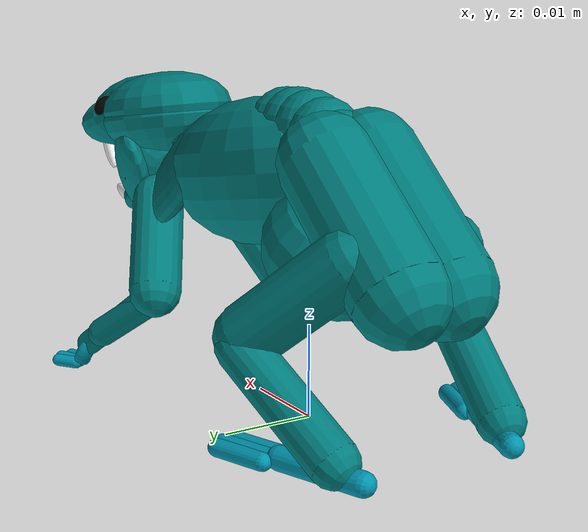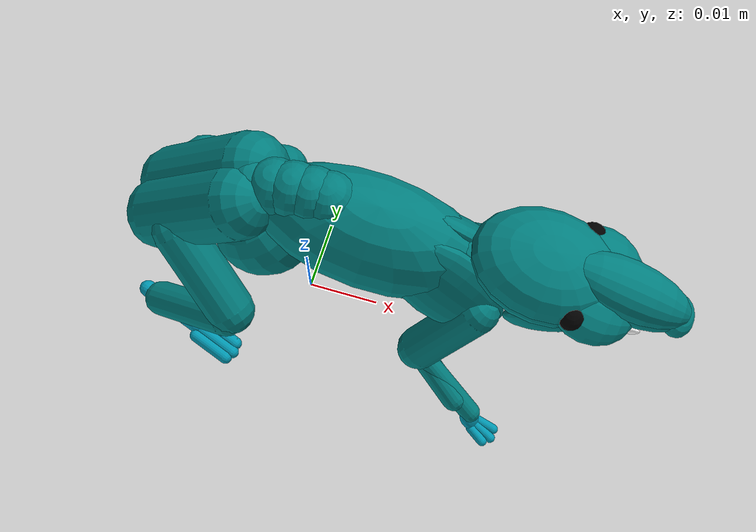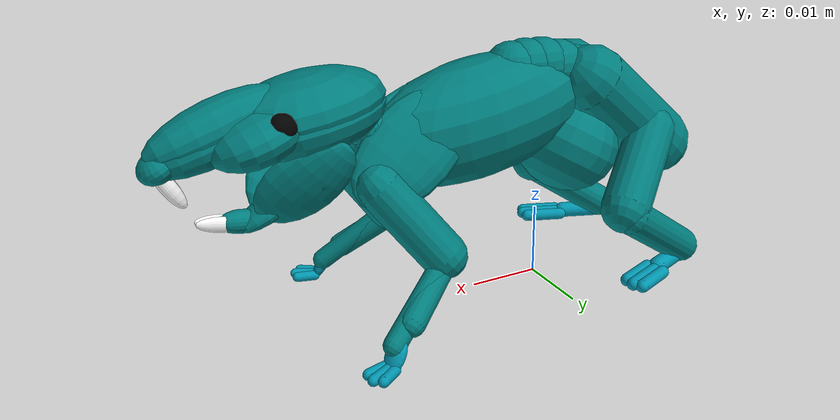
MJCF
<mujoco model="mouse_MA_anatomical03">
  <compiler angle="radian" autolimits="true"/>
  <size njmax="8000" nconmax="4000"/>
  <default>
    <joint limited="true" solreflimit="0.01 1" solimplimit="0.99 0.9999 0" armature="4.75e-09" damping="0.001"/>
    <geom friction="0.7 0.005 0.0001" solref="0.005 1"/>
    <site group="3" rgba="0 0 1 1"/>
    <general ctrllimited="true" ctrlrange="-1 1" gainprm="0.01"/>
    <default class="bone">
      <geom contype="0" conaffinity="0" group="0" rgba="0.5 0.5 0.5 1" density="1100.0"/>
    </default>
    <default class="collision">
      <geom contype="1" conaffinity="1" condim="1" group="2"/>
      <default class="collision_primitive">
        <geom type="capsule" group="2" rgba="0 0.5 0.5 1" density="500.0"/>
        <default class="collision_primitive_paw">
          <geom condim="3" priority="1" rgba="0 0.6 0.7 1" friction="1.5 0.005 0.0001"/>
        </default>
        <default class="nonself_collision_primitive">
          <geom conaffinity="0"/>
        </default>
      </default>
    </default>
    <default class="lumbar">
      <joint group="3" pos="0.00114 0 -0.00114" armature="7.92e-08" damping="0.03"/>
      <general gainprm="0.15"/>
      <default class="lumbar_extend">
        <joint stiffness="0.02" range="-0.5235987755982988 0.7853981633974483"/>
        <tendon range="-1 1"/>
        <general gainprm="0.4"/>
      </default>
      <default class="lumbar_bend">
        <joint stiffness="0.03" range="-0.5235987755982988 0.5235987755982988"/>
        <tendon range="-1 1"/>
      </default>
      <default class="lumbar_twist">
        <joint stiffness="0.03" range="-0.5235987755982988 0.5235987755982988"/>
        <tendon range="-1 1"/>
      </default>
    </default>
    <default class="cervical">
      <joint group="3" pos="-0.0076 0 -0.019" stiffness="1.0" armature="7.92e-06" damping="1.0"/>
      <default class="cervical_extend">
        <joint range="-0.4072434921320102 0.6108652381980153"/>
        <tendon range="-1 1"/>
        <general gainprm="2.5"/>
      </default>
      <default class="cervical_bend">
        <joint range="-0.6108652381980153 0.6108652381980153"/>
        <tendon range="-1 1"/>
        <general gainprm="2.5"/>
      </default>
      <default class="cervical_twist">
        <joint range="-0.6108652381980153 0.6108652381980153"/>
        <tendon range="-1 1"/>
        <general gainprm="2.5"/>
      </default>
    </default>
    <default class="atlas">
      <joint axis="0 -1 0" stiffness="0.002" range="-0.08726646259971647 0.7853981633974483" damping="0.002"/>
      <general gainprm="0.025"/>
    </default>
    <default class="mandible">
      <joint stiffness="0.002" range="-0.296705972839036 0.2617993877991494" springref="-0.314159265359" damping="0.002"/>
      <general gainprm="0.025"/>
    </default>
    <default class="caudal">
      <joint group="3" stiffness="1e-05" damping="0.002"/>
      <general gainprm="0.005"/>
      <default class="caudal_extend">
        <joint range="-0.08726646259971647 0.08726646259971647"/>
        <tendon range="-0.05 0.05"/>
      </default>
      <default class="caudal_bend">
        <joint range="-0.08726646259971647 0.08726646259971647"/>
        <tendon range="-0.2 0.2"/>
      </default>
    </default>
    <default class="hip">
      <joint armature="7.92e-08" damping="0.02"/>
      <general gainprm="0.2"/>
      <default class="hip_supinate">
        <joint range="-0.6981317007977318 0.5235987755982988"/>
      </default>
      <default class="hip_abduct">
        <joint range="-0.5235987755982988 1.047197551196598"/>
      </default>
      <default class="hip_extend">
        <joint range="-1.570796326794897 1.047197551196598"/>
        <general gainprm="0.3"/>
      </default>
    </default>
    <default class="knee">
      <joint range="-1.221730476396031 1.53588974175501" damping="0.005"/>
      <general gainprm="0.2"/>
    </default>
    <default class="ankle">
      <joint range="-0.1396263401595464 1.396263401595464" damping="0.003"/>
      <general gainprm="0.2"/>
    </default>
    <default class="toe">
      <joint range="0 0.8726646259971648" damping="0.001"/>
      <general gainprm="0.025"/>
    </default>
    <default class="scapula">
      <joint damping="0.005"/>
      <general gainprm="0.25"/>
      <default class="scapula_supinate">
        <joint pos="0 0.0019 0" range="-0.0174532925199433 0.1745329251994329"/>
      </default>
      <default class="scapula_abduct">
        <joint pos="0 0.0019 -0.0038" range="-0.2617993877991494 0.2617993877991494"/>
      </default>
      <default class="scapula_extend">
        <joint pos="0 0 0" range="-0.03490658503988659 0.03490658503988659"/>
        <general gainprm="0.25"/>
      </default>
    </default>
    <default class="shoulder">
      <joint range="-1.308996938995747 0.8726646259971648" damping="0.005"/>
      <general gainprm="0.15"/>
    </default>
    <default class="shoulder_sup">
      <joint range="-0.05235987755982989 1.134464013796314" damping="0.005"/>
      <general gainprm="0.15"/>
    </default>
    <default class="elbow">
      <joint range="-1.308996938995747 0.6981317007977318" damping="0.003"/>
      <general gainprm="0.15"/>
    </default>
    <default class="wrist">
      <joint range="-0.3490658503988659 2.094395102393195" damping="0.002"/>
      <general gainprm="0.05"/>
    </default>
    <default class="finger">
      <joint range="0 1.570796326794897" damping="0.002"/>
      <general gainprm="0.025"/>
    </default>
    <default class="sensor">
      <site group="4"/>
    </default>
  </default>
  <statistic meansize="0.00114"/>
  <asset>
  </asset>
  <worldbody>
    <camera name="close_fixed" mode="fixed" pos="0.114 -0.114 0.1216" xyaxes="1 1 0 -1 1 2"/>
    <camera name="close_profile_aligned" mode="targetbody" pos="0.114 -0.114 0.095" target="torso"/>
    <body name="torso" pos="0.011778 7.8224e-08 0.024734">
      <light name="tracking_light" mode="trackcom" pos="0 0 1.14"/>
      <camera name="back" mode="trackcom" pos="-0.38 0 0.19" xyaxes="0 -1 0 1 0 2"/>
      <camera name="side" mode="trackcom" pos="0 -0.38 0.19" xyaxes="1 0 0 0 1 2"/>
      <camera name="top" mode="trackcom" fovy="100.0" pos="0 0 0.38" zaxis="0 -0.2 1"/>
      <camera name="close_profile" mode="trackcom" pos="0.114 -0.114 0.095" xyaxes="1 1 0 -1 1 2"/>
      <camera name="close_side" mode="trackcom" pos="0 -0.114 0.095" xyaxes="0 0 1 0 1 2"/>
      <camera name="examples" mode="trackcom" pos="-0.19 0 0.057" xyaxes="0 -1 0 1 0 2"/>
      <camera name="stretch_examples" mode="trackcom" pos="0.19 0 0.019" xyaxes="0 1 0 -1 0 4"/>
      <!-- REVISED - Smaller and shifted forward -->
      <geom name="collision_torso" class="nonself_collision_primitive" type="ellipsoid" size="0.016 0.0075 0.008" density="468.251260009" pos="-0.002 0 0" euler="0 0.1745329251994329 0"/>
      <body name="vertebra_1" pos="-0.007288 -7.1453e-08 0.006402">
        <geom name="vertebra_1_collision" class="nonself_collision_primitive" type="sphere" size="0.0038" pos="0 0 -0.0006232"/>
        <body name="vertebra_2" pos="-0.002139 9.8602e-07 0.0002022">
          <geom name="vertebra_2_collision" class="nonself_collision_primitive" type="sphere" size="0.0038" pos="0 0 -0.0006232"/>
          <body name="vertebra_3" pos="-0.002477 -3.956e-06 -3.5975e-05">
            <geom name="vertebra_3_collision" class="nonself_collision_primitive" type="sphere" size="0.0038" pos="0 0 -0.0006232"/>
            <body name="vertebra_4" pos="-0.002575 3.3235e-06 -0.0004937">
              <geom name="vertebra_4_collision" class="nonself_collision_primitive" type="sphere" size="0.0038" pos="0 0 -0.0006232"/>
              <body name="vertebra_5" pos="-0.002618 -2.3576e-06 -0.0009493">
                <geom name="vertebra_5_collision" class="nonself_collision_primitive" type="sphere" size="0.0038" pos="0 0 -0.0006232"/>
                <body name="vertebra_6" pos="-0.00235 -1.9967e-06 -0.001384">
                  <geom name="vertebra_6_collision" class="nonself_collision_primitive" type="sphere" size="0.0038" pos="0 0 -0.0006232"/>
                  <joint name="vertebra_6_twist" class="lumbar_twist" axis="1 0 0"/>
                  <body name="pelvis" pos="-0.004967 1.335e-06 -0.003086">
                    <geom name="collision_pelvis_L" class="nonself_collision_primitive" size="0.00494 0.00798 0" density="1548.57736929" pos="-0.0003116 0.0024928 -0.0021812" euler="0 0.8726646259971648 0"/>
                    <geom name="collision_pelvis_R" class="nonself_collision_primitive" size="0.00494 0.00798 0" density="1548.57736929" pos="-0.0003116 -0.0024928 -0.0021812" euler="0 0.8726646259971648 0"/>
                    <geom name="collision_pelvis_gut" class="nonself_collision_primitive" type="ellipsoid" size="0.0076 0.0076 0.00684" density="1548.57736929" pos="0.00779 0 -0.006232" euler="0 -0.5235987755982988 0"/>
                    <site name="hip_L" size="0.000836" pos="-0.001828 0.004367 -0.003757"/>
                    <site name="hip_R" size="0.000836" pos="-0.001828 -0.004367 -0.003757"/>
                    <body name="upper_leg_L" pos="-0.001828 0.004367 -0.003757">
                      <joint name="hip_L_supinate" class="hip_supinate" axis="-0 -0 1"/>
                      <joint name="hip_L_abduct" class="hip_abduct" axis="1 -0 -0"/>
                      <joint name="hip_L_extend" class="hip_extend" axis="0 1 0"/>
                      <site name="knee_L" type="cylinder" size="0.000228 0.00152" pos="0.005861 0.006642 -0.009768" zaxis="0 1 0"/>
                      <geom name="upper_leg_L0_collision" class="collision_primitive" size="0.003322 0.006644" density="1561.75550556" pos="0.003269 0.004086 -0.004903" euler="0.6108652381980153 -0.6981317007977318 0"/>
                      <body name="lower_leg_L" pos="0.005861 0.006642 -0.009768">
                        <joint name="knee_L" class="knee" axis="0.5 -1 0"/>
                        <site name="ankle_L" type="cylinder" size="0.000228 0.000988" pos="-0.012275 -0.001796 -0.008383" zaxis="0 1 0"/>
                        <body name="foot_L" pos="-0.012275 -0.001796 -0.008383">
                          <joint name="ankle_L" class="ankle" axis="-0.3 1 0"/>
                          <geom name="foot_L_collision" class="collision_primitive_paw" size="0.00122 0.004706" density="2041.15978228" pos="0.003144 0.0008575 -0.0008575" euler="1.570796326794897 -1.221730476396031 0"/>
                          <site name="toe_L" type="cylinder" size="0.000228 0.0019" pos="0.007982 0.002893 -0.001046" zaxis="0 1 0"/>
                          <body name="toe_L" pos="0.007982 0.002893 -0.001046">
                            <joint name="toe_L" class="toe" axis="0 1 0"/>
                            <geom name="toe_L0_collision" class="collision_primitive_paw" size="0.0009056 0.002756" pos="0.003229 -0.0003229 0" euler="1.570796326794897 -1.221730476396031 0"/>
                            <geom name="toe_L1_collision" class="collision_primitive_paw" size="0.0009056 0.002953" pos="0.003067 0.0009686 0" euler="1.570796326794897 -1.221730476396031 0"/>
                            <geom name="toe_L2_collision" class="collision_primitive_paw" size="0.0009056 0.002756" pos="0.002583 0.002099 0" euler="1.570796326794897 -1.221730476396031 0"/>
                            <site name="sole_L" class="sensor" type="box" size="0.00228 0.00152 0.00076" pos="0.003116 0.0009348 -0.0006232" euler="0 0 0.3490658503988659"/>
                          </body>
                        </body>
                        <geom name="lower_leg_L_collision" class="collision_primitive" size="0.002492 0.007309" density="1302.86687267" pos="-0.00466 -0.0000465 -0.004073" quat="0.5843939876140521 0.278581552273902 0.3900453953818352 0.6547828460754284"/>
                      </body>
                    </body>
                    <body name="upper_leg_R" pos="-0.001828 -0.004367 -0.003757">
                      <joint name="hip_R_supinate" class="hip_supinate" axis="0 0 -1"/>
                      <joint name="hip_R_abduct" class="hip_abduct" axis="-1 0 0"/>
                      <joint name="hip_R_extend" class="hip_extend" axis="0 1 0"/>
                      <site name="knee_R" type="cylinder" size="0.000228 0.00152" pos="0.005861 -0.006642 -0.009768" zaxis="0 1 0"/>
                      <geom name="upper_leg_R0_collision" class="collision_primitive" size="0.003322 0.006644" density="1561.75550556" pos="0.003269 -0.004086 -0.004903" euler="-0.6108652381980153 -0.6981317007977318 0"/>
                      <body name="lower_leg_R" pos="0.005861 -0.006642 -0.009768">
                        <joint name="knee_R" class="knee" axis="-0.5 -1 0"/>
                        <site name="ankle_R" type="cylinder" size="0.000228 0.000988" pos="-0.012275 0.001796 -0.008383" zaxis="0 1 0"/>
                        <body name="foot_R" pos="-0.012275 0.001796 -0.008383">
                          <joint name="ankle_R" class="ankle" axis="0.3 1 0"/>
                          <geom name="foot_R_collision" class="collision_primitive_paw" size="0.00122 0.004706" density="2041.15978228" pos="0.003144 -0.0008575 -0.0008575" euler="1.570796326794897 1.221730476396031 0"/>
                          <site name="toe_R" type="cylinder" size="0.000228 0.0019" pos="0.007982 -0.002893 -0.001046" zaxis="0 1 0"/>
                          <body name="toe_R" pos="0.007982 -0.002893 -0.001046">
                            <joint name="toe_R" class="toe" axis="0 1 0"/>
                            <geom name="toe_R0_collision" class="collision_primitive_paw" size="0.0009056 0.002756" pos="0.003229 0.0003229 0" euler="1.570796326794897 1.221730476396031 0"/>
                            <geom name="toe_R1_collision" class="collision_primitive_paw" size="0.0009056 0.002953" pos="0.003067 -0.0009686 0" euler="1.570796326794897 1.221730476396031 0"/>
                            <geom name="toe_R2_collision" class="collision_primitive_paw" size="0.0009056 0.002756" pos="0.002583 -0.002099 0" euler="1.570796326794897 1.221730476396031 0"/>
                            <site name="sole_R" class="sensor" type="box" size="0.00228 0.00152 0.00076" pos="0.003116 -0.0009348 -0.0006232" euler="0 0 -0.3490658503988659"/>
                          </body>
                        </body>
                        <geom name="lower_leg_R_collision" class="collision_primitive" size="0.002492 0.007309" density="1302.86687267" pos="-0.004571 -0.0000614 -0.004018" quat="0.6564315036111004 0.3901417719765998 0.2779576926818845 0.5827749135856758"/>
                      </body>
                    </body>
                    <body name="vertebra_C1" pos="-0.005990 0 -0.004515">
                      <body name="vertebra_C2" pos="-0.001473 0 -0.001606">
                        <body name="vertebra_C3" pos="-0.001301 0 -0.001620">
                          <body name="vertebra_C4" pos="-0.001243 0 -0.001678">
                            <body name="vertebra_C5" pos="-0.001207 0 -0.001736">
                              <body name="vertebra_C6" pos="-0.001185 0 -0.001862">
                                <body name="vertebra_C7" pos="-0.001222 0 -0.002145">
                                  <body name="vertebra_C8" pos="-0.001309 0 -0.002097">
                                    <body name="vertebra_C9" pos="-0.001628 0 -0.001944">
                                      <body name="vertebra_C10" pos="-0.001847 0 -0.001734">
                                        <body name="vertebra_C11" pos="-0.002042 0 -0.001658">
                                          <body name="vertebra_C12" pos="-0.002331 0 -0.001460">
                                            <body name="vertebra_C13" pos="-0.002621 0 -0.0009851">
                                              <body name="vertebra_C14" pos="-0.002594 0 -0.0003454">
                                                <body name="vertebra_C15" pos="-0.002480 0 -0.0001198">
                                                  <body name="vertebra_C16" pos="-0.002544 0 -0.0000526">
                                                    <body name="vertebra_C17" pos="-0.002464 0 -0.00000635">
                                                      <body name="vertebra_C18" pos="-0.002359 0 6.937e-11">
                                                        <body name="vertebra_C19" pos="-0.002358 0 -3.1167e-10">
                                                          <body name="vertebra_C20" pos="-0.002367 0 9.5628e-07">
                                                            <body name="vertebra_C21" pos="-0.002325 0 -0.00004167">
                                                            <body name="vertebra_C22" pos="-0.002473 0 -0.000004985">
                                                            <body name="vertebra_C23" pos="-0.002428 0 6.6553e-10">
                                                            <body name="vertebra_C24" pos="-0.002349 0 -4.7391e-10">
                                                            <body name="vertebra_C25" pos="-0.002268 0 5.242e-11">
                                                            <body name="vertebra_C26" pos="-0.002139 0 -5.1894e-10">
                                                            <body name="vertebra_C27" pos="-0.001973 0 5.3036e-10">
                                                            <body name="vertebra_C28" pos="-0.001914 0 1.9281e-07">
                                                            <body name="vertebra_C29" pos="-0.001814 0 -2.3581e-11">
                                                            <body name="vertebra_C30" pos="-0.001522 0 -1.5949e-07">
                                                            <geom name="vertebra_C30_collision" class="collision_primitive" size="0.0004932 0.002342 0.001313" density="507.157357703" pos="-1.2973e-17 0 0" quat="0 0.7071067811865475 0 0.7071067811865476" rgba="0 0 0 0"/>
                                                            </body>
                                                            <joint name="vertebra_C29_bend" class="caudal_bend" pos="0.001421 0 1.8478e-11" axis="1.299892892972596e-08 0 -0.9999999999999999" range="-0.2617993877991494 0.2617993877991494"/>
                                                            <geom name="vertebra_C29_collision" class="collision_primitive" size="0.0004928 0.002266 0.0009951" density="507.157357703" pos="8.6486e-18 0 0" quat="0 0.7071067811865475 0 0.7071067811865476" rgba="0 0 0 0"/>
                                                            </body>
                                                            <geom name="vertebra_C28_collision" class="collision_primitive" size="0.0004928 0.002191 0.001093" density="507.157357703" pos="-8.6486e-18 0 0" quat="0 0.7071067811865475 0 0.7071067811865476" rgba="0 0 0 0"/>
                                                            </body>
                                                            <joint name="vertebra_C27_extend" class="caudal_extend" pos="0.001464 0 -3.9358e-10" axis="0 0.9999999999999999 0" range="-0.2617993877991494 0.2617993877991494"/>
                                                            <geom name="vertebra_C27_collision" class="collision_primitive" size="0.0005242 0.002115 0.001163" density="507.157357703" pos="-8.6486e-18 -2.1622e-18 0" quat="0 0.7071067811865475 0 0.7071067811865476" rgba="0 0 0 0"/>
                                                            </body>
                                                            <geom name="vertebra_C26_collision" class="collision_primitive" size="0.0005242 0.00204 0.001163" density="507.157357703" pos="0 0 0" quat="0 0.7071067811865475 0 0.7071067811865476" rgba="0 0 0 0"/>
                                                            </body>
                                                            <joint name="vertebra_C25_bend" class="caudal_bend" pos="0.001367 0 -3.1587e-11" axis="-2.311404765380703e-08 0 -0.9999999999999998" range="-0.2617993877991494 0.2617993877991494"/>
                                                            <geom name="vertebra_C25_collision" class="collision_primitive" size="0.0005242 0.001964 0.001322" density="507.157357703" pos="8.6486e-18 2.1622e-18 0" quat="0 0.7071067811865475 0 0.7071067811865476" rgba="0 0 0 0"/>
                                                            </body>
                                                            <geom name="vertebra_C24_collision" class="collision_primitive" size="0.0005242 0.001888 0.001322" density="507.157357703" pos="0 2.1622e-18 0" quat="0 0.7071067811865475 0 0.7071067811865476" rgba="0 0 0 0"/>
                                                            </body>
                                                            <joint name="vertebra_C23_extend" class="caudal_extend" pos="0.001367 0 -3.7451e-10" axis="0 1 0" range="-0.2617993877991494 0.2617993877991494"/>
                                                            <geom name="vertebra_C23_collision" class="collision_primitive" size="0.0005242 0.001813 0.001421" density="507.157357703" pos="0 0 0" quat="0 0.7071067811865475 0 0.7071067811865476" rgba="0 0 0 0"/>
                                                            </body>
                                                            <geom name="vertebra_C22_collision" class="collision_primitive" size="0.0005242 0.001737 0.001421" density="507.157357703" pos="8.6486e-18 0 0" quat="0 0.7071067811865475 0 0.7071067811865476" rgba="0 0 0 0"/>
                                                            </body>
                                                            <joint name="vertebra_C21_bend" class="caudal_bend" pos="0.001468 0 0.00002631" axis="0.01792297618959377 0 -0.9998393705613454" range="-0.2617993877991494 0.2617993877991494"/>
                                                            <geom name="vertebra_C21_collision" class="collision_primitive" size="0.0005816 0.001889 0.001464" density="507.157357703" pos="-8.6486e-18 0 0" quat="0 0.7071067811865475 0 0.7071067811865476" rgba="0 0 0 0"/>
                                                            </body>
                                                            <geom name="vertebra_C20_collision" class="collision_primitive" size="0.0005693 0.001967 0.001367" density="507.157357703" pos="0 1.0811e-18 0" quat="0 0.7071067811865475 0 0.7071067811865476" rgba="0 0 0 0"/>
                                                          </body>
                                                          <joint name="vertebra_C19_extend" class="caudal_extend" pos="0.001626 0 2.1493e-10" axis="-0 1 0" range="-0.2617993877991494 0.2617993877991494"/>
                                                          <geom name="vertebra_C19_collision" class="collision_primitive" size="0.0006209 0.001965 0.001367" density="507.157357703" pos="0 0 0" quat="0 0.7071067811865475 0 0.7071067811865476" rgba="0 0 0 0"/>
                                                        </body>
                                                        <geom name="vertebra_C18_collision" class="collision_primitive" size="0.0006209 0.001867 0.001367" density="507.157357703" pos="-1.7297e-17 1.3513e-19 0" quat="0 0.7071067811865475 0 0.7071067811865476" rgba="0 0 0 0"/>
                                                      </body>
                                                      <joint name="vertebra_C17_bend" class="caudal_bend" pos="0.001626 0 0.000004189" axis="0.002575715973669538 0 -0.9999966828381097" range="-0.2617993877991494 0.2617993877991494"/>
                                                      <geom name="vertebra_C17_collision" class="collision_primitive" size="0.0006209 0.001769 0.001367" density="507.157357703" pos="1.7297e-17 1.3513e-19 0" quat="0 0.7071067811865475 0 0.7071067811865476" rgba="0 0 0 0"/>
                                                    </body>
                                                    <geom name="vertebra_C16_collision" class="collision_primitive" size="0.0007137 0.00167 0.001469" density="507.157357703" pos="1.7297e-17 0 0" quat="0 0.7071067811865475 0 0.7071067811865476" rgba="0 0 0 0"/>
                                                  </body>
                                                  <joint name="vertebra_C15_extend" class="caudal_extend" pos="0.001494 0 0.00007221" axis="-0 0.9999999999999999 0" range="-0.2617993877991494 0.2617993877991494"/>
                                                  <geom name="vertebra_C15_collision" class="collision_primitive" size="0.0007012 0.001572 0.001468" density="507.157357703" pos="0 -1.0811e-18 0" quat="-3.048411496515643e-15 0.6991848455046811 3.117107305228081e-15 0.7149409428873096" rgba="0 0 0 0"/>
                                                </body>
                                                <geom name="vertebra_C14_collision" class="collision_primitive" size="0.0007011 0.001474 0.001468" density="507.157357703" pos="-1.7297e-17 -1.6216e-18 0" quat="0 0.6866112770928985 0 0.7270247273434782" rgba="0 0 0 0"/>
                                              </body>
                                              <joint name="vertebra_C13_bend" class="caudal_bend" pos="0.001335 0 0.0005016" axis="0.3518244833508478 0 -0.9360659874789323" range="-0.2617993877991494 0.2617993877991494"/>
                                              <geom name="vertebra_C13_collision" class="collision_primitive" size="0.0007945 0.001505 0.001626" density="507.157357703" pos="-4.3243e-18 0 6.7567e-20" quat="1.892164903646171e-16 0.6293932092262298 -2.336181429597261e-16 0.7770869888113604" rgba="0 0 0 0"/>
                                            </body>
                                            <geom name="vertebra_C12_collision" class="collision_primitive" size="0.0009247 0.001576 0.001626" density="507.157357703" pos="0 0 0" quat="1.235560731911126e-17 0.5080793265726891 -7.288463628123299e-18 0.8613102796956755" rgba="0 0 0 0"/>
                                          </body>
                                          <joint name="vertebra_C11_extend" class="caudal_extend" pos="0.00104 0 0.0008445" axis="-0 0.9999999999999998 0" range="-0.2617993877991494 0.2617993877991494"/>
                                          <geom name="vertebra_C11_collision" class="collision_primitive" size="0.0009499 0.001481 0.001626" density="507.157357703" pos="-8.6486e-18 0 0" quat="8.0408085539503e-17 0.4349444185915732 -3.883920751947562e-17 0.9004573020060631" rgba="0 0 0 0"/>
                                        </body>
                                        <geom name="vertebra_C10_collision" class="collision_primitive" size="0.0013 0.001975 0.001496" density="507.157357703" pos="0 0 -5.4054e-19" quat="6.606927199194023e-17 0.404822478038031 -2.925028864881283e-17 0.914395298147988" rgba="0 0 0 0"/>
                                      </body>
                                      <joint name="vertebra_C9_bend" class="caudal_bend" pos="0.001097 0 0.001309" axis="0.7665487416508834 0 -0.6421861308635113" range="-0.2617993877991494 0.2617993877991494"/>
                                      <geom name="vertebra_C9_collision" class="collision_primitive" size="0.00119 0.001708 0.001496" density="507.157357703" pos="0 0 -1.0811e-18" quat="0.9339363308955284 -2.188685129702187e-17 0.3574394072194587 5.718710691193161e-17" rgba="0 0 0 0"/>
                                    </body>
                                    <geom name="vertebra_C8_collision" class="collision_primitive" size="0.001146 0.001504 0.001496" density="507.157357703" pos="0 0 -1.0811e-18" quat="0.9557562961254608 -1.801208397451436e-17 0.2941596546376485 5.852319444074877e-17" rgba="0 0 0 0"/>
                                  </body>
                                  <joint name="vertebra_C7_extend" class="caudal_extend" pos="0.001022 0 0.001794" axis="-0 0.9999999999999998 0" range="-0.2617993877991494 0.2617993877991494"/>
                                  <geom name="vertebra_C7_collision" class="collision_primitive" size="0.001238 0.001763 0.001426" density="507.157357703" pos="0 0 0" quat="-0.9587181623873691 -0.02864387142163538 -0.2629262253293439 0.1044452668751926" rgba="0 0 0 0"/>
                                </body>
                                <joint name="vertebra_C6_extend" class="caudal_extend" pos="0.0007993 0 0.001256" axis="-0 0.9999999999999998 0" range="-0.2617993877991494 0.2617993877991494"/>
                                <joint name="vertebra_C6_bend" class="caudal_bend" pos="0.0007993 0 0.001256" axis="0.8436498258045544 0 -0.5368938176398985" range="-0.2617993877991494 0.2617993877991494"/>
                                <geom name="vertebra_C6_collision" class="collision_primitive" size="0.001463 0.001688 0.001489" density="507.157357703" pos="0 0 -2.1622e-18" quat="-0.9684724633255426 -0.0201653665451908 -0.2338356379719502 0.08351850206094803" rgba="0 0 0 0"/>
                              </body>
                              <joint name="vertebra_C5_extend" class="caudal_extend" pos="0.0007647 0 0.0011" axis="-0 0.9999999999999998 0" range="-0.2617993877991494 0.2617993877991494"/>
                              <joint name="vertebra_C5_bend" class="caudal_bend" pos="0.0007647 0 0.0011" axis="0.8211323953906199 0 -0.5707377587299287" range="-0.2617993877991494 0.2617993877991494"/>
                              <geom name="vertebra_C5_collision" class="collision_primitive" size="0.001727 0.001435 0.00134" density="507.157357703" pos="0 0 0" quat="0.959555122982002 -1.723817788817547e-17 0.2815208091047534 5.875580549826768e-17" rgba="0 0 0 0"/>
                            </body>
                            <joint name="vertebra_C4_extend" class="caudal_extend" pos="0.0009637 0 0.001301" axis="-0 0.9999999999999996 0" range="-0.2617993877991494 0.2617993877991494"/>
                            <joint name="vertebra_C4_bend" class="caudal_bend" pos="0.0009637 0 0.001301" axis="0.8035447758282259 0 -0.595244313907462" range="-0.2617993877991494 0.2617993877991494"/>
                            <geom name="vertebra_C4_collision" class="collision_primitive" size="0.002528 0.001464 0.001619" density="507.157357703" pos="0 0 -2.1622e-18" quat="0.6698964656770412 0.2263597253784533 0.2263597253784533 0.6698964656770412" rgba="0 0 0 0"/>
                          </body>
                          <joint name="vertebra_C3_extend" class="caudal_extend" pos="0.00107 0 0.001332" axis="-0 0.9999999999999998 0" range="-0.2617993877991494 0.2617993877991494"/>
                          <joint name="vertebra_C3_bend" class="caudal_bend" pos="0.00107 0 0.001332" axis="0.7796571863505312 0 -0.6262065727633115" range="-0.2617993877991494 0.2617993877991494"/>
                          <geom name="vertebra_C3_collision" class="collision_primitive" size="0.002991 0.001557 0.001708" density="507.157357703" pos="0 0 2.1622e-18" quat="0.658413368499565 0.2578601097127201 0.2578601097127201 0.658413368499565" rgba="0 0 0 0"/>
                        </body>
                        <joint name="vertebra_C2_extend" class="caudal_extend" pos="0.001352 0 0.001474" axis="-0 1 0" range="-0.2617993877991494 0.2617993877991494"/>
                        <joint name="vertebra_C2_bend" class="caudal_bend" pos="0.001352 0 0.001474" axis="0.7369087259505994 0 -0.6759922555901543" range="-0.2617993877991494 0.2617993877991494"/>
                        <geom name="vertebra_C2_collision" class="collision_primitive" size="0.003177 0.001332 0.002" density="507.157357703" pos="0 0 0" quat="0.6165945006583455 0.3461375763448482 0.3461375763448482 0.6165945006583455" rgba="0 0 0 0"/>
                      </body>
                      <joint name="vertebra_C1_extend" class="caudal_extend" pos="0.00165 0 0.001242" axis="0 1 0" range="-0.2617993877991494 0.2617993877991494"/>
                      <joint name="vertebra_C1_bend" class="caudal_bend" pos="0.00165 0 0.001242" axis="0.6012684687925202 0 -0.7990470752314273" range="-0.2617993877991494 0.2617993877991494"/>
                      <geom name="vertebra_C1_collision" class="collision_primitive" size="0.004167 0.000891 0.002065" density="507.157357703" pos="0 -1.0557e-21 0" quat="0.5772408551843025 0.3506607415056362 0.3240276763775721 0.662447057819841" rgba="0 0 0 0"/>
                    </body>
                  </body>
                </body>
                <joint name="vertebra_5_bend" class="lumbar_bend" axis="0 0 1"/>
              </body>
              <joint name="vertebra_4_extend" class="lumbar_extend" axis="0 1 0"/>
            </body>
            <joint name="vertebra_3_twist" class="lumbar_twist" axis="1 0 0"/>
          </body>
          <joint name="vertebra_2_bend" class="lumbar_bend" axis="0 0 1"/>
        </body>
        <joint name="vertebra_1_extend" class="lumbar_extend" axis="0 1 0"/>
      </body>
      <body name="vertebra_cervical_5" pos="0.01053 4.494e-06 -0.0003801">
        <geom name="vertebra_cervical_5_collision" class="nonself_collision_primitive" type="sphere" size="0.00342" density="300.0"/>
        <body name="vertebra_cervical_4" pos="0.0009154 -4.5657e-06 0.0003076">
          <geom name="vertebra_cervical_4_collision" class="nonself_collision_primitive" type="sphere" size="0.003192" density="300.0"/>
          <body name="vertebra_cervical_3" pos="0.0008171 4.591e-11 0.0003578">
            <geom name="vertebra_cervical_3_collision" class="nonself_collision_primitive" type="sphere" size="0.002964" density="300.0"/>
            <body name="vertebra_cervical_2" pos="0.000722 4.879e-11 0.0003324">
              <geom name="vertebra_cervical_2_collision" class="nonself_collision_primitive" type="sphere" size="0.002736" density="300.0"/>
              <body name="vertebra_cervical_1" pos="0.0006755 1.7184e-10 0.0003553">
                <geom name="vertebra_cervical_1_collision" class="nonself_collision_primitive" type="sphere" size="0.002508" density="300.0"/>
                <body name="vertebra_axis" pos="0.0007153 -6.6753e-07 0.0006482">
                  <geom name="vertebra_axis_collision" class="nonself_collision_primitive" type="sphere" size="0.00228" density="300.0"/>
                  <body name="vertebra_atlant" pos="0.0009318 6.6765e-07 0.0005204">
                    <geom name="vertebra_atlant_collision" class="nonself_collision_primitive" type="sphere" size="0.002052" density="300.0"/>
                    <joint name="vertebra_atlant_extend" class="cervical_extend" pos="0.00001041 -1.883e-08 -0.00008038" axis="0 1 0"/>
                    <body name="skull" pos="0.009344 1.5128e-09 0.0006374">
                      <geom name="skull_0_collision" class="collision_primitive" type="ellipsoid" size="0.009722 0.007346 0.0044" density="703.10773841" pos="-0.003986 0 0.0003608" euler="0 0.1745329251994329 0"/>
                      <geom name="skull_0b_collision" class="collision_primitive" type="ellipsoid" size="0.009722 0.007346 0.0044" density="1.40621547682" pos="-0.003986 0 0.001443" euler="0 0.1745329251994329 0"/>
                      <geom name="skull_F_collision" class="collision_primitive" type="ellipsoid" size="0.00316 0.003918 0.0088" density="703.10773841" pos="0.006378 0 -0.0003608" euler="0 1.919862177193763 0"/>
                      <geom name="skull_Fb_collision" class="collision_primitive" type="ellipsoid" size="0.00316 0.003918 0.0088" density="1.40621547682" pos="0.006378 0 0.0007216" euler="0 1.919862177193763 0"/>
                      <geom name="skull_L_collision" class="collision_primitive" type="ellipsoid" size="0.00316 0.005877 0.00616" density="703.10773841" pos="0.002392 0.002008 -0.0003608" euler="0 1.919862177193763 0"/>
                      <geom name="eye_L_collision" class="collision_primitive" type="sphere" group="1" size="0.00176 0.00176 0.00176" rgba="0 0 0 1" pos="0.0004861 0.005632 0.0011"/>
                      <geom name="skull_R_collision" class="collision_primitive" type="ellipsoid" size="0.00316 0.005877 0.00616" density="703.10773841" pos="0.002392 -0.002008 -0.0003608" euler="0 1.919862177193763 0"/>
                      <geom name="eye_R_collision" class="collision_primitive" type="sphere" group="1" size="0.00176 0.00176 0.00176" rgba="0 0 0 1" pos="0.0004861 -0.005632 0.0011"/>
                      <geom name="skull_P0_collision" class="collision_primitive" type="box" size="0.002917 0.002743 0.000704" density="703.10773841" pos="0.0007972 0 -0.002526"/>
                      <geom name="skull_P1_collision" class="collision_primitive" type="box" size="0.001944 0.001763 0.000528" density="703.10773841" pos="0.00279 0 -0.002526"/>
                      <geom name="skull_P2_collision" class="collision_primitive" type="box" size="0.0004861 0.001469 0.000352" density="703.10773841" pos="0.003787 0 -0.002526"/>
                      <geom name="skull_T0_collision" class="collision_primitive" type="ellipsoid" size="0.002431 0.002938 0.00176" density="703.10773841" pos="0.01315 0 -0.002886" euler="0 0.5235987755982988 0"/>
                      <geom name="skull_T1_collision" class="collision_primitive" type="ellipsoid" group="1" size="0.0009722 0.0007346 0.00308" rgba="1 1 1 1" density="703.10773841" pos="0.01236 0.0004016 -0.005412" euler="0 0.5235987755982988 0"/>
                      <geom name="skull_T2_collision" class="collision_primitive" type="ellipsoid" group="1" size="0.0009722 0.0007346 0.00308" rgba="1 1 1 1" density="703.10773841" pos="0.01236 -0.0004016 -0.005412" euler="0 0.5235987755982988 0"/>
                      <joint name="atlas" class="atlas" pos="-0.01251 0 0"/>
                      <site name="head" class="sensor" type="box" size="0.00088 0.00088 0.00088"/>
                      <camera name="egocentric" fovy="80.0" pos="0.0044 0 0.0022" euler="0 -1.570796326794897 -1.570796326794897"/>
                      <body name="jaw" pos="0.0001993 -6.9907e-09 -0.007216" euler="0 0.2617993877991494 0">
                        <geom name="jaw_back_collision" class="collision_primitive" type="ellipsoid" size="0.005347 0.005877 0.00308" density="314.057274977" pos="-0.004783 0 0.000902" euler="0 0.9599310885968813 0"/>
                        <geom name="jaw_F_collision" class="collision_primitive" type="ellipsoid" size="0.001458 0.002938 0.00528" density="314.057274977" pos="0.001196 0 -0.002165" euler="0 1.832595714594046 0"/>
                        <geom name="jaw_L_collision" class="collision_primitive" type="ellipsoid" size="0.004375 0.001714 0.00704" density="314.057274977" pos="-0.002392 0.003614 0.0003608" euler="-0.6981317007977318 2.181661564992912 0.5235987755982988"/>
                        <geom name="jaw_R_collision" class="collision_primitive" type="ellipsoid" size="0.004375 0.001714 0.00704" density="314.057274977" pos="-0.002392 -0.003614 0.0003608" euler="0.6981317007977318 2.181661564992912 -0.5235987755982988"/>
                        <geom name="jaw_T0_collision" class="collision_primitive" type="ellipsoid" size="0.001458 0.001469 0.00264" density="314.057274977" pos="0.00558 0 -0.002526" euler="0 1.221730476396031 0"/>
                        <geom name="jaw_T1_collision" class="collision_primitive" type="ellipsoid" group="1" size="0.0009722 0.0005877 0.00308" rgba="1 1 1 1" density="314.057274977" pos="0.007573 0.0004016 -0.001804" euler="0 1.134464013796314 0"/>
                        <geom name="jaw_T2_collision" class="collision_primitive" type="ellipsoid" group="1" size="0.0009722 0.0005877 0.00308" rgba="1 1 1 1" density="314.057274977" pos="0.007573 -0.0004016 -0.001804" euler="0 1.134464013796314 0"/>
                        <geom name="jaw_P0_collision" class="collision_primitive" type="box" size="0.002917 0.002743 0.000704" density="314.057274977" pos="-0.001196 0 0.0003608" euler="0 0.9599310885968813 0"/>
                        <geom name="jaw_P1_collision" class="collision_primitive" type="box" size="0.001944 0.002155 0.00044" density="314.057274977" pos="0 0 -0.000433" euler="0 0.5235987755982988 0"/>
                        <geom name="jaw_P2_collision" class="collision_primitive" type="box" size="0.001944 0.001763 0.00044" density="314.057274977" pos="0.001196 0 -0.00101" euler="0 0.4363323129985824 0"/>
                        <geom name="jaw_P3_collision" class="collision_primitive" type="box" size="0.001458 0.001273 0.000264" density="314.057274977" pos="0.002073 0 -0.001263" euler="0 0.2617993877991494 0"/>
                        <joint name="mandible" class="mandible" pos="-0.00814 0 0.00176" axis="0 1 0"/>
                      </body>
                    </body>
                  </body>
                  <joint name="vertebra_axis_twist" class="cervical_twist" pos="0.00003779 2.7863e-08 -0.0001017" axis="0.7409845944832573 -0.0006915153935393208 0.6715216694529994"/>
                </body>
                <joint name="vertebra_cervical_1_bend" class="cervical_bend" pos="0.00001044 -8.4268e-12 -0.0001002" axis="-0.4655674978646318 0 0.885012375581277"/>
              </body>
              <joint name="vertebra_cervical_2_extend" class="cervical_extend" pos="0.000004922 -2.2022e-12 -0.00009647" axis="0 1 0"/>
            </body>
            <joint name="vertebra_cervical_3_twist" class="cervical_twist" pos="0.000003115 -1.849e-12 -0.00009668" axis="0.9160353567291684 5.146827584715309e-08 0.4010975258239107"/>
          </body>
          <joint name="vertebra_cervical_4_bend" class="cervical_bend" pos="-0.000005843 1.8229e-07 -0.0001037" axis="-0.3185475796000196 0 0.9478950836057671"/>
        </body>
        <joint name="vertebra_cervical_5_extend" class="cervical_extend" pos="-0.00007351 -1.5195e-07 -0.00008728" axis="0 1 0"/>
      </body>
      <body name="scapula_L" pos="0.002493 0.0006232 0.004362">
        <joint name="scapula_L_supinate" class="scapula_supinate" pos="0 -0.0019 0" axis="-0 -0 1"/>
        <joint name="scapula_L_abduct" class="scapula_abduct" pos="0 -0.0019 -0.0038" axis="1 -0 -0"/>
        <joint name="scapula_L_extend" class="scapula_extend" pos="0 0 0" axis="0.3 1 0"/>
        <site name="shoulder_L" size="0.00076" pos="0.010906 0.003739 -0.00966"/>
        <body name="upper_arm_L" pos="0.010906 0.003739 -0.00966">
          <joint name="shoulder_L" class="shoulder" axis="0 1 0"/>
          <joint name="shoulder_sup_L" class="shoulder_sup" axis="0 0 -1"/>
          <site name="elbow_L" type="cylinder" size="0.000228 0.00152" pos="-0.006054 0.003935 -0.008475" zaxis="0 1 0.2"/>
          <body name="lower_arm_L" pos="-0.006054 0.003935 -0.008475">
            <joint name="elbow_L" class="elbow" axis="0 1 0.2"/>
            <site name="wrist_L" type="cylinder" size="0.000304 0.001292" pos="0.008209 0.004789 -0.007525" zaxis="0 1 0"/>
            <body name="hand_L" pos="0.008209 0.004789 -0.007525">
              <joint name="wrist_L" class="wrist" axis="0.6 -1 0"/>
              <geom name="hand_L_collision" class="collision_primitive_paw" type="ellipsoid" size="0.002459 0.001405 0.000843" density="2531.78122831" pos="0.000576 0.000288 -0.001728" euler="-0.6981317007977318 0.8726646259971648 0.7853981633974483"/>
              <site name="finger_L" type="cylinder" size="0.000228 0.0019" pos="0.001152 0.000576 -0.003168" zaxis="-0.2 1 0"/>
              <body name="finger_L" pos="0.001152 0.000576 -0.003168">
                <joint name="finger_L" class="finger" axis="-0.5 1 0"/>
                <geom name="finger_L0_collision" class="collision_primitive_paw" size="0.0007025 0.001229" pos="0.001872 -0.000288 0" euler="1.570796326794897 -1.308996938995747 0"/>
                <geom name="finger_L1_collision" class="collision_primitive_paw" size="0.0007025 0.001405" pos="0.001728 0.000720 -0.000000" euler="1.570796326794897 -1.099557428756428 0"/>
                <geom name="finger_L2_collision" class="collision_primitive_paw" size="0.0007025 0.001229" pos="0.001008 0.00144 -0.000000" euler="1.570796326794897 -0.9599310885968813 0"/>
                <site name="palm_L" class="sensor" type="box" size="0.00152 0.00152 0.00076" pos="0.00187 0.000935 -0.000623" euler="0 0 0.4886921905584123"/>
              </body>
            </body>
            <geom name="radius_L_collision" class="collision_primitive" size="0.001418 0.006048" pos="0.004372 0.002603 -0.004646" quat="0.02376493230846292 0.7917721441518218 0.4232293467931716 0.4397829234413568"/>
            <geom name="ulna_L_collision" class="collision_primitive" size="0.001668 0.005005" pos="0.002565 0.001897 -0.003606" quat="0.01282244452041863 0.7446249872782607 0.4776065607195328 0.4661128472752391"/>
          </body>
          <geom name="humerus_L_collision" class="collision_primitive" size="0.002953 0.005906" pos="-0.002942 0.002199 -0.004554" quat="0.472560999180163 0.3450082805420177 0.0007016050154913519 0.8109592444517103"/>
        </body>
        <geom name="scapula_L_collision" class="nonself_collision_primitive" type="ellipsoid" size="0.001902 0.00556 0.009238" density="513.564612303" pos="0.006677 0.003282 -0.005787" quat="0.1844194062696375 0.7692222855376651 0.4740322845517004 0.3867556738123709"/>
      </body>
      <body name="scapula_R" pos="0.002493 -0.0006232 0.004362">
        <joint name="scapula_R_supinate" class="scapula_supinate" pos="0 0.0019 0" axis="0 0 -1"/>
        <joint name="scapula_R_abduct" class="scapula_abduct" pos="0 0.0019 -0.0038" axis="-1 0 0"/>
        <joint name="scapula_R_extend" class="scapula_extend" pos="0 0 0" axis="-0.3 1 0"/>
        <site name="shoulder_R" size="0.00076" pos="0.010906 -0.003739 -0.00966"/>
        <body name="upper_arm_R" pos="0.010906 -0.003739 -0.00966">
          <joint name="shoulder_R" class="shoulder" axis="0 1 0"/>
          <joint name="shoulder_sup_R" class="shoulder_sup" axis="-0 -0 1"/>
          <site name="elbow_R" type="cylinder" size="0.000228 0.00152" pos="-0.006054 -0.003935 -0.008475" zaxis="0 1 -0.2"/>
          <body name="lower_arm_R" pos="-0.006054 -0.003935 -0.008475">
            <joint name="elbow_R" class="elbow" axis="0 1 -0.2"/>
            <site name="wrist_R" type="cylinder" size="0.000304 0.001292" pos="0.008209 -0.004789 -0.007525" zaxis="0 1 0"/>
            <body name="hand_R" pos="0.008209 -0.004789 -0.007525">
              <joint name="wrist_R" class="wrist" axis="-0.6 -1 0"/>
              <geom name="hand_R_collision" class="collision_primitive_paw" type="ellipsoid" size="0.002459 0.001405 0.000843" density="2531.78122831" pos="0.000576 -0.000288 -0.001728" euler="0.6981317007977318 0.8726646259971648 -0.7853981633974483"/>
              <site name="finger_R" type="cylinder" size="0.000228 0.0019" pos="0.001152 -0.000576 -0.003168" zaxis="0.2 1 0"/>
              <body name="finger_R" pos="0.001152 -0.000576 -0.003168">
                <joint name="finger_R" class="finger" axis="0.5 1 0"/>
                <geom name="finger_R0_collision" class="collision_primitive_paw" size="0.0007025 0.001229" pos="0.001872 0.000288 0" euler="1.570796326794897 1.308996938995747 0"/>
                <geom name="finger_R1_collision" class="collision_primitive_paw" size="0.0007025 0.001405" pos="0.001728 -0.000720 0" euler="1.570796326794897 1.099557428756428 0"/>
                <geom name="finger_R2_collision" class="collision_primitive_paw" size="0.0007025 0.001229" pos="0.001008 -0.00144 0" euler="1.570796326794897 0.9599310885968813 0"/>
                <site name="palm_R" class="sensor" type="box" size="0.00152 0.00152 0.00076" pos="0.00187 -0.000935 -0.000623" euler="0 0 -0.4886921905584123"/>
              </body>
            </body>
            <geom name="radius_R_collision" class="collision_primitive" size="0.001418 0.006048" pos="0.004372 -0.002603 -0.004646" quat="0.4397828585901176 0.423230473256099 0.7917715587074765 0.02376557635859348"/>
            <geom name="ulna_R_collision" class="collision_primitive" size="0.001668 0.005005" pos="0.002565 -0.001897 -0.003606" quat="0.4661127828257156 0.4776067795325061 0.7446248854693838 0.01282254930824632"/>
          </body>
          <geom name="humerus_R_collision" class="collision_primitive" size="0.002953 0.005906" pos="-0.002942 -0.0022 -0.004554" quat="0.8109593935310486 0.0007013948082913995 0.3450082795040448 0.4725607444157158"/>
        </body>
        <geom name="scapula_R_collision" class="nonself_collision_primitive" type="ellipsoid" size="0.001902 0.00556 0.009238" density="513.564646393" pos="0.006677 -0.003282 -0.005787" quat="0.3867556972129688 0.4740321312040688 0.7692223496423682 0.1844194839763772"/>
      </body>
    </body>
  </worldbody>
  <contact>
    <exclude name="pelvis:vertebra_C2" body1="pelvis" body2="vertebra_C2"/>
    <exclude name="pelvis:vertebra_C3" body1="pelvis" body2="vertebra_C3"/>
    <exclude name="pelvis:vertebra_C4" body1="pelvis" body2="vertebra_C4"/>
    <exclude name="vertebra_C1:vertebra_C3" body1="vertebra_C1" body2="vertebra_C3"/>
    <exclude name="vertebra_C1:vertebra_C4" body1="vertebra_C1" body2="vertebra_C4"/>
    <exclude name="vertebra_C2:vertebra_C4" body1="vertebra_C2" body2="vertebra_C4"/>
    <exclude name="vertebra_C3:vertebra_C5" body1="vertebra_C3" body2="vertebra_C5"/>
    <exclude name="vertebra_C4:vertebra_C6" body1="vertebra_C4" body2="vertebra_C6"/>
    <exclude name="vertebra_C5:vertebra_C7" body1="vertebra_C5" body2="vertebra_C7"/>
    <exclude name="vertebra_axis:skull" body1="vertebra_axis" body2="skull"/>
    <exclude name="pelvis:vertebra_C5" body1="pelvis" body2="vertebra_C5"/>
    <exclude name="pelvis:vertebra_C6" body1="pelvis" body2="vertebra_C6"/>
    <exclude name="vertebra_C2:vertebra_C5" body1="vertebra_C2" body2="vertebra_C5"/>
    <exclude name="vertebra_C3:vertebra_C6" body1="vertebra_C3" body2="vertebra_C6"/>
    <exclude name="vertebra_C4:vertebra_C7" body1="vertebra_C4" body2="vertebra_C7"/>
    <exclude name="upper_arm_L:upper_arm_R" body1="upper_arm_L" body2="upper_arm_R"/>
    <exclude name="upper_leg_L:vertebra_C1" body1="upper_leg_L" body2="vertebra_C1"/>
    <exclude name="upper_leg_L:vertebra_C2" body1="upper_leg_L" body2="vertebra_C2"/>
    <exclude name="upper_leg_R:vertebra_C1" body1="upper_leg_R" body2="vertebra_C1"/>
    <exclude name="upper_leg_R:vertebra_C2" body1="upper_leg_R" body2="vertebra_C2"/>
    <exclude name="vertebra_cervical_1:skull" body1="vertebra_cervical_1" body2="skull"/>
    <exclude name="vertebra_cervical_2:skull" body1="vertebra_cervical_2" body2="skull"/>
    <exclude name="upper_arm_L:torso" body1="upper_arm_L" body2="torso"/>
    <exclude name="upper_arm_R:torso" body1="upper_arm_R" body2="torso"/>
    <exclude name="lower_leg_L:pelvis" body1="lower_leg_L" body2="pelvis"/>
    <exclude name="lower_leg_R:pelvis" body1="lower_leg_R" body2="pelvis"/>
  </contact>
  <tendon>
    <fixed name="lumbar_extend" class="lumbar_extend">
      <joint joint="vertebra_1_extend" coef="0.604983465832"/>
      <joint joint="vertebra_4_extend" coef="0.395016534168"/>
    </fixed>
    <fixed name="lumbar_bend" class="lumbar_bend">
      <joint joint="vertebra_2_bend" coef="0.658212326553"/>
      <joint joint="vertebra_5_bend" coef="0.341787673447"/>
    </fixed>
    <fixed name="lumbar_twist" class="lumbar_twist">
      <joint joint="vertebra_3_twist" coef="0.570669983621"/>
      <joint joint="vertebra_6_twist" coef="0.429330016379"/>
    </fixed>
    <fixed name="cervical_extend" class="cervical_extend">
      <joint joint="vertebra_cervical_5_extend" coef="0.341713547174"/>
      <joint joint="vertebra_cervical_2_extend" coef="0.332408292936"/>
      <joint joint="vertebra_atlant_extend" coef="0.32587815989"/>
    </fixed>
    <fixed name="cervical_bend" class="cervical_bend">
      <joint joint="vertebra_cervical_4_bend" coef="0.50743949691"/>
      <joint joint="vertebra_cervical_1_bend" coef="0.49256050309"/>
    </fixed>
    <fixed name="cervical_twist" class="cervical_twist">
      <joint joint="vertebra_cervical_3_twist" coef="0.496142185731"/>
      <joint joint="vertebra_axis_twist" coef="0.503857814269"/>
    </fixed>
    <fixed name="caudal_extend" class="caudal_extend">
      <joint joint="vertebra_C1_extend" coef="0.29007246307"/>
      <joint joint="vertebra_C2_extend" coef="0.207669040031"/>
      <joint joint="vertebra_C3_extend" coef="0.151635169821"/>
      <joint joint="vertebra_C4_extend" coef="0.115426643422"/>
      <joint joint="vertebra_C5_extend" coef="0.0875497823386"/>
      <joint joint="vertebra_C6_extend" coef="0.0692562920379"/>
      <joint joint="vertebra_C7_extend" coef="0.0558691633464"/>
      <joint joint="vertebra_C11_extend" coef="0.0175306632713"/>
      <joint joint="vertebra_C15_extend" coef="0.00414417378836"/>
      <joint joint="vertebra_C19_extend" coef="0.00074642278889"/>
      <joint joint="vertebra_C23_extend" coef="8.5912797067e-05"/>
      <joint joint="vertebra_C27_extend" coef="1.42732873368e-05"/>
    </fixed>
    <fixed name="caudal_bend" class="caudal_bend">
      <joint joint="vertebra_C1_bend" coef="0.370792881126"/>
      <joint joint="vertebra_C2_bend" coef="0.233517805262"/>
      <joint joint="vertebra_C3_bend" coef="0.150894350178"/>
      <joint joint="vertebra_C4_bend" coef="0.101885012096"/>
      <joint joint="vertebra_C5_bend" coef="0.0671743532429"/>
      <joint joint="vertebra_C6_bend" coef="0.0439561223709"/>
      <joint joint="vertebra_C9_bend" coef="0.0188199119629"/>
      <joint joint="vertebra_C13_bend" coef="0.00999889819861"/>
      <joint joint="vertebra_C17_bend" coef="0.00252642968052"/>
      <joint joint="vertebra_C21_bend" coef="0.000378783618491"/>
      <joint joint="vertebra_C25_bend" coef="4.10656566522e-05"/>
      <joint joint="vertebra_C29_bend" coef="1.43866075466e-05"/>
    </fixed>
  </tendon>
  <actuator>
    <general name="lumbar_extend" forcerange="-20 20" tendon="lumbar_extend" dyntype="filter" biastype="affine" dynprm="0.04" gainprm="13.08996938995747" biasprm="2.617993877991495 -20"/>
    <general name="lumbar_bend" forcerange="-20 20" tendon="lumbar_bend" dyntype="filter" biastype="affine" dynprm="0.04" gainprm="10.47197551196598" biasprm="0 -20"/>
    <general name="lumbar_twist" forcerange="-20 20" tendon="lumbar_twist" dyntype="filter" biastype="affine" dynprm="0.04" gainprm="10.47197551196598" biasprm="0 -20"/>
    <general name="cervical_extend" forcerange="-20 20" tendon="cervical_extend" dyntype="filter" biastype="affine" dynprm="0.04" gainprm="10.18108730330026" biasprm="2.03621746066005 -20"/>
    <general name="cervical_bend" forcerange="-20 20" tendon="cervical_bend" dyntype="filter" biastype="affine" dynprm="0.04" gainprm="12.21730476396031" biasprm="0 -20"/>
    <general name="cervical_twist" forcerange="-20 20" tendon="cervical_twist" dyntype="filter" biastype="affine" dynprm="0.04" gainprm="12.21730476396031" biasprm="0 -20"/>
    <general name="caudal_extend" forcerange="-0.1 0.1" tendon="caudal_extend" dyntype="filter" biastype="affine" dynprm="0.04" gainprm="0.02617993877991495" biasprm="0 -0.1"/>
    <general name="caudal_bend" forcerange="-0.1 0.1" tendon="caudal_bend" dyntype="filter" biastype="affine" dynprm="0.04" gainprm="0.02617993877991494" biasprm="0 -0.1"/>
    <general name="hip_L_supinate" forcerange="-0.2 0.2" joint="hip_L_supinate" dyntype="filter" biastype="affine" dynprm="0.04" gainprm="0.2443460952792061" biasprm="-0.0349065850398866 -0.4"/>
    <general name="hip_L_abduct" forcerange="-0.2 0.2" joint="hip_L_abduct" dyntype="filter" biastype="affine" dynprm="0.04" gainprm="0.3141592653589793" biasprm="0.1047197551196598 -0.4"/>
    <general name="hip_L_extend" forcerange="-0.3 0.3" joint="hip_L_extend" dyntype="filter" biastype="affine" dynprm="0.04" gainprm="0.7853981633974482" biasprm="-0.1570796326794897 -0.6"/>
    <general name="knee_L" forcerange="-0.2 0.2" joint="knee_L" dyntype="filter" biastype="affine" dynprm="0.04" gainprm="0.5515240436302081" biasprm="0.06283185307179587 -0.4"/>
    <general name="ankle_L" forcerange="-0.2 0.2" joint="ankle_L" dyntype="filter" biastype="affine" dynprm="0.04" gainprm="0.307177948351002" biasprm="0.2513274122871835 -0.4"/>
    <general name="toe_L" forcerange="-0.025 0.025" joint="toe_L" dyntype="filter" biastype="affine" dynprm="0.04" gainprm="0.02181661564992912" biasprm="0.02181661564992912 -0.05"/>
    <general name="hip_R_supinate" forcerange="-0.2 0.2" joint="hip_R_supinate" dyntype="filter" biastype="affine" dynprm="0.04" gainprm="0.2443460952792061" biasprm="-0.0349065850398866 -0.4"/>
    <general name="hip_R_abduct" forcerange="-0.2 0.2" joint="hip_R_abduct" dyntype="filter" biastype="affine" dynprm="0.04" gainprm="0.3141592653589793" biasprm="0.1047197551196598 -0.4"/>
    <general name="hip_R_extend" forcerange="-0.3 0.3" joint="hip_R_extend" dyntype="filter" biastype="affine" dynprm="0.04" gainprm="0.7853981633974482" biasprm="-0.1570796326794897 -0.6"/>
    <general name="knee_R" forcerange="-0.2 0.2" joint="knee_R" dyntype="filter" biastype="affine" dynprm="0.04" gainprm="0.5515240436302081" biasprm="0.06283185307179587 -0.4"/>
    <general name="ankle_R" forcerange="-0.2 0.2" joint="ankle_R" dyntype="filter" biastype="affine" dynprm="0.04" gainprm="0.307177948351002" biasprm="0.2513274122871835 -0.4"/>
    <general name="toe_R" forcerange="-0.025 0.025" joint="toe_R" dyntype="filter" biastype="affine" dynprm="0.04" gainprm="0.02181661564992912" biasprm="0.02181661564992912 -0.05"/>
    <general name="atlas" forcerange="-0.025 0.025" joint="atlas" dyntype="filter" biastype="affine" dynprm="0.04" gainprm="0.02181661564992912" biasprm="0.0174532925199433 -0.05"/>
    <general name="mandible" forcerange="-0.025 0.025" joint="mandible" dyntype="filter" biastype="affine" dynprm="0.04" gainprm="0.01396263401595464" biasprm="-0.000872664625997166 -0.05"/>
    <general name="scapula_L_supinate" forcerange="-0.25 0.25" joint="scapula_L_supinate" dyntype="filter" biastype="affine" dynprm="0.04" gainprm="0.04799655442984406" biasprm="0.03926990816987241 -0.5"/>
    <general name="scapula_L_abduct" forcerange="-0.25 0.25" joint="scapula_L_abduct" dyntype="filter" biastype="affine" dynprm="0.04" gainprm="0.1308996938995747" biasprm="0 -0.5"/>
    <general name="scapula_L_extend" forcerange="-0.25 0.25" joint="scapula_L_extend" dyntype="filter" biastype="affine" dynprm="0.04" gainprm="0.0174532925199433" biasprm="0 -0.5"/>
    <general name="shoulder_L" forcerange="-0.15 0.15" joint="shoulder_L" dyntype="filter" biastype="affine" dynprm="0.04" gainprm="0.3272492347489368" biasprm="-0.06544984694978737 -0.3"/>
    <general name="shoulder_sup_L" forcerange="-0.15 0.15" joint="shoulder_sup_L" dyntype="filter" biastype="affine" dynprm="0.04" gainprm="0.1780235837034216" biasprm="0.1623156204354726 -0.3"/>
    <general name="elbow_L" forcerange="-0.15 0.15" joint="elbow_L" dyntype="filter" biastype="affine" dynprm="0.04" gainprm="0.3010692959690218" biasprm="-0.0916297857297023 -0.3"/>
    <general name="wrist_L" forcerange="-0.05 0.05" joint="wrist_L" dyntype="filter" biastype="affine" dynprm="0.04" gainprm="0.1221730476396031" biasprm="0.08726646259971647 -0.1"/>
    <general name="finger_L" forcerange="-0.025 0.025" joint="finger_L" dyntype="filter" biastype="affine" dynprm="0.04" gainprm="0.03926990816987241" biasprm="0.03926990816987241 -0.05"/>
    <general name="scapula_R_supinate" forcerange="-0.25 0.25" joint="scapula_R_supinate" dyntype="filter" biastype="affine" dynprm="0.04" gainprm="0.04799655442984406" biasprm="0.03926990816987241 -0.5"/>
    <general name="scapula_R_abduct" forcerange="-0.25 0.25" joint="scapula_R_abduct" dyntype="filter" biastype="affine" dynprm="0.04" gainprm="0.1308996938995747" biasprm="0 -0.5"/>
    <general name="scapula_R_extend" forcerange="-0.25 0.25" joint="scapula_R_extend" dyntype="filter" biastype="affine" dynprm="0.04" gainprm="0.0174532925199433" biasprm="0 -0.5"/>
    <general name="shoulder_R" forcerange="-0.15 0.15" joint="shoulder_R" dyntype="filter" biastype="affine" dynprm="0.04" gainprm="0.3272492347489368" biasprm="-0.06544984694978737 -0.3"/>
    <general name="shoulder_sup_R" forcerange="-0.15 0.15" joint="shoulder_sup_R" dyntype="filter" biastype="affine" dynprm="0.04" gainprm="0.1780235837034216" biasprm="0.1623156204354726 -0.3"/>
    <general name="elbow_R" forcerange="-0.15 0.15" joint="elbow_R" dyntype="filter" biastype="affine" dynprm="0.04" gainprm="0.3010692959690218" biasprm="-0.0916297857297023 -0.3"/>
    <general name="wrist_R" forcerange="-0.05 0.05" joint="wrist_R" dyntype="filter" biastype="affine" dynprm="0.04" gainprm="0.1221730476396031" biasprm="0.08726646259971647 -0.1"/>
    <general name="finger_R" forcerange="-0.025 0.025" joint="finger_R" dyntype="filter" biastype="affine" dynprm="0.04" gainprm="0.03926990816987241" biasprm="0.03926990816987241 -0.05"/>
  </actuator>
  <sensor>
    <accelerometer name="accelerometer" site="head"/>
    <velocimeter name="velocimeter" site="head"/>
    <gyro name="gyro" site="head"/>
    <touch name="palm_L" site="palm_L"/>
    <touch name="palm_R" site="palm_R"/>
    <touch name="sole_L" site="sole_L"/>
    <touch name="sole_R" site="sole_R"/>
    <subtreelinvel name="torso" body="torso"/>
  </sensor>
  <compiler meshdir="./"/>
</mujoco>
